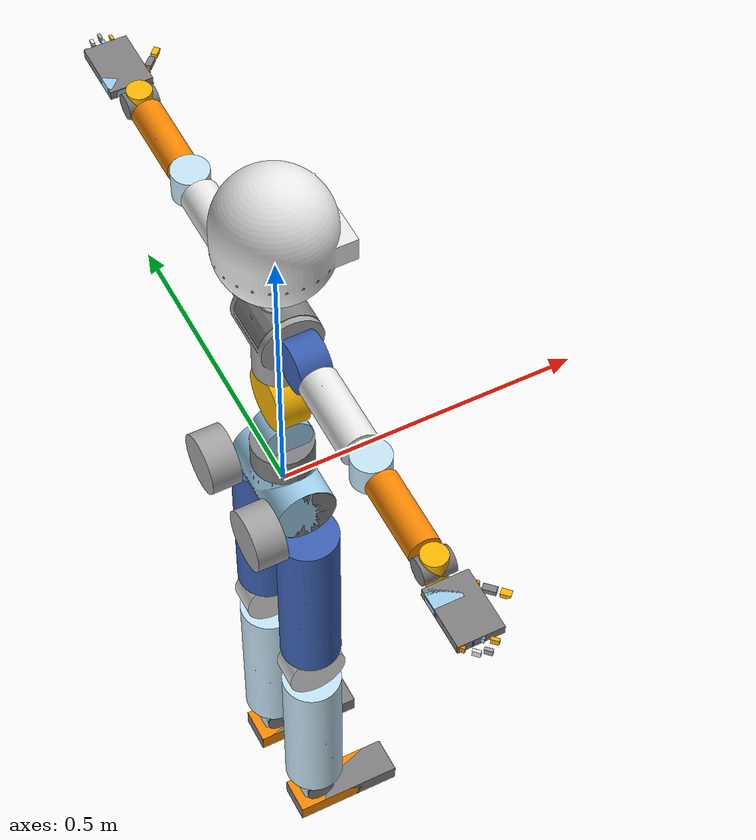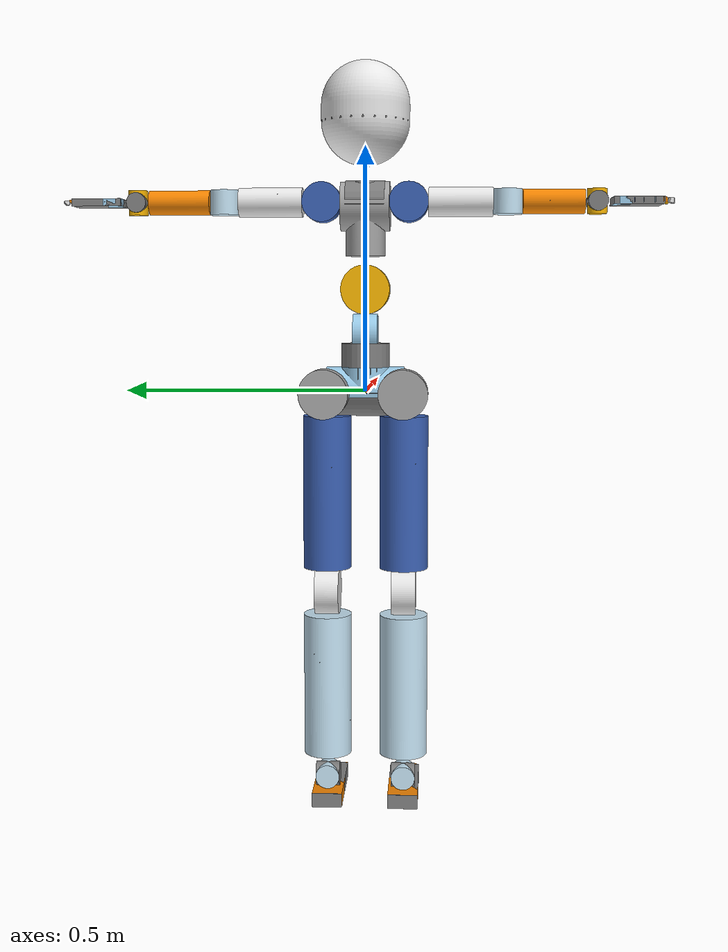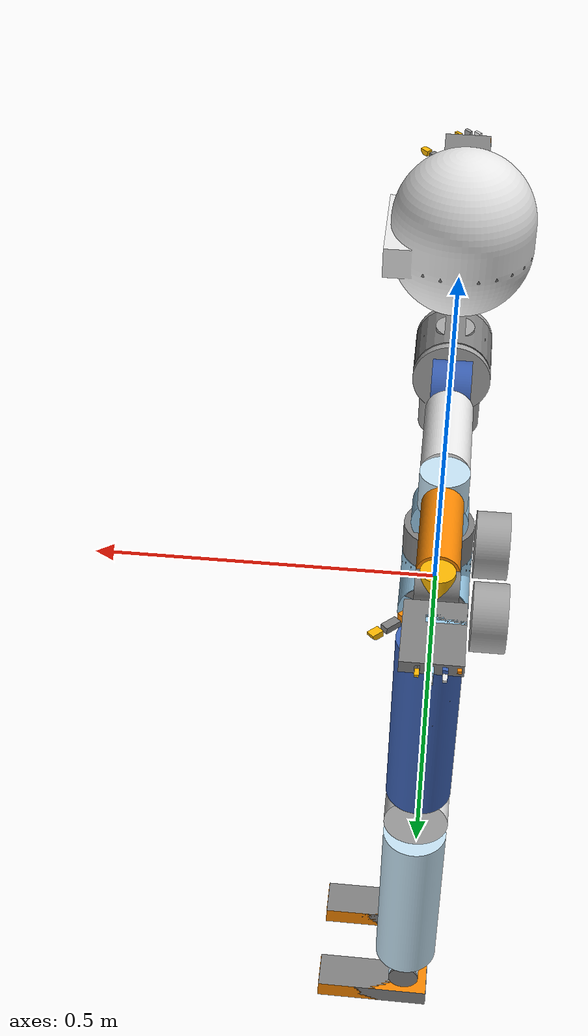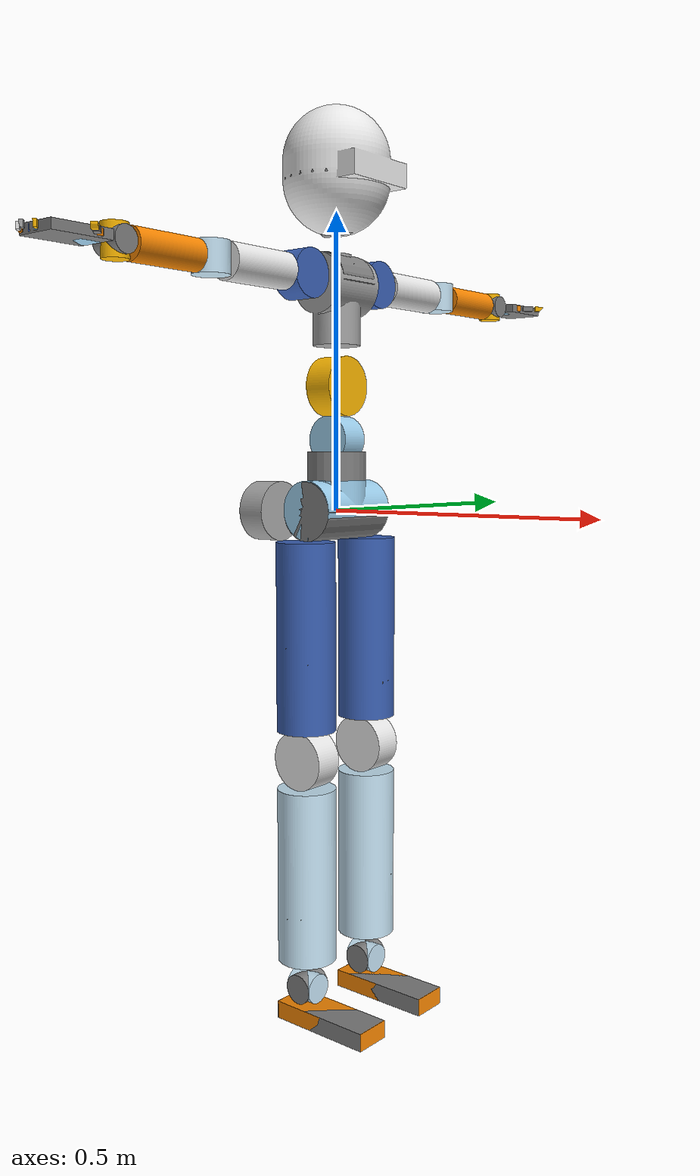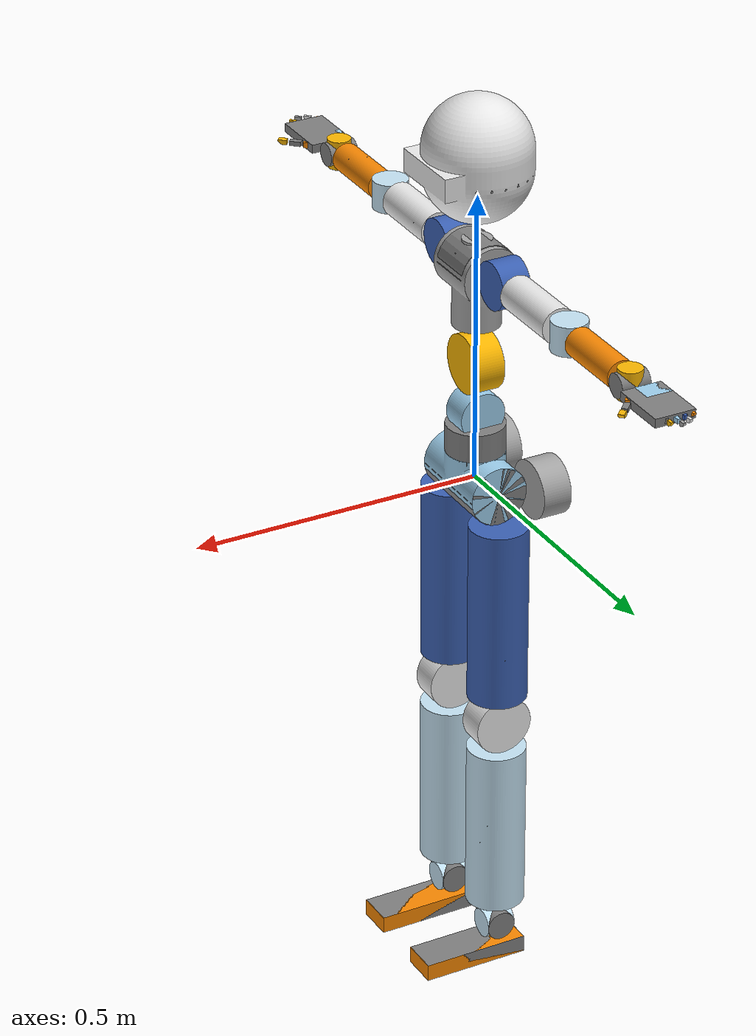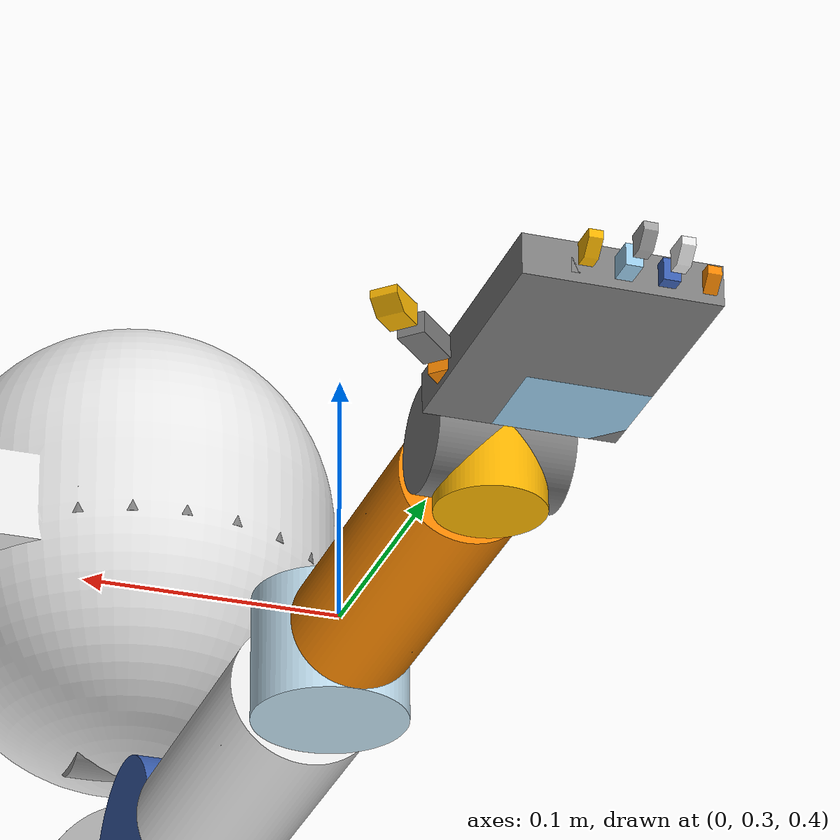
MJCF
<?xml version='1.0' encoding='utf-8'?>
<mujoco model="miku">
  <compiler angle="radian" meshdir="../meshes/" />

  <asset>
    <mesh name="pelvis_visual" content_type="model/stl" file="pelvis_visual.stl" />
    <mesh name="left_hip_pitch_visual" content_type="model/stl" file="left_hip_pitch_visual.stl" />
    <mesh name="left_hip_roll_visual" content_type="model/stl" file="left_hip_roll_visual.stl" />
    <mesh name="left_hip_yaw_visual" content_type="model/stl" file="left_hip_yaw_visual.stl" />
    <mesh name="left_knee_pitch_visual" content_type="model/stl" file="left_knee_pitch_visual.stl" />
    <mesh name="left_ankle_yaw_visual" content_type="model/stl" file="left_ankle_yaw_visual.stl" />
    <mesh name="left_ankle_roll_visual" content_type="model/stl" file="left_ankle_roll_visual.stl" />
    <mesh name="left_foot_visual" content_type="model/stl" file="left_foot_visual.stl" />
    <mesh name="right_hip_pitch_visual" content_type="model/stl" file="right_hip_pitch_visual.stl" />
    <mesh name="right_hip_roll_visual" content_type="model/stl" file="right_hip_roll_visual.stl" />
    <mesh name="right_hip_yaw_visual" content_type="model/stl" file="right_hip_yaw_visual.stl" />
    <mesh name="right_knee_pitch_visual" content_type="model/stl" file="right_knee_pitch_visual.stl" />
    <mesh name="right_ankle_yaw_visual" content_type="model/stl" file="right_ankle_yaw_visual.stl" />
    <mesh name="right_ankle_roll_visual" content_type="model/stl" file="right_ankle_roll_visual.stl" />
    <mesh name="right_foot_visual" content_type="model/stl" file="right_foot_visual.stl" />
    <mesh name="waist_yaw_visual" content_type="model/stl" file="waist_yaw_visual.stl" />
    <mesh name="waist_pitch_visual" content_type="model/stl" file="waist_pitch_visual.stl" />
    <mesh name="torso_visual" content_type="model/stl" file="torso_visual.stl" />
    <mesh name="left_shoulder_pitch_visual" content_type="model/stl"
      file="left_shoulder_pitch_visual.stl" />
    <mesh name="left_shoulder_roll_visual" content_type="model/stl"
      file="left_shoulder_roll_visual.stl" />
    <mesh name="left_shoulder_yaw_visual" content_type="model/stl"
      file="left_shoulder_yaw_visual.stl" />
    <mesh name="left_elbow_pitch_visual" content_type="model/stl" file="left_elbow_pitch_visual.stl" />
    <mesh name="left_wrist_yaw_visual" content_type="model/stl" file="left_wrist_yaw_visual.stl" />
    <mesh name="left_wrist_roll_visual" content_type="model/stl" file="left_wrist_roll_visual.stl" />
    <mesh name="left_hand_visual" content_type="model/stl" file="left_hand_visual.stl" />
    <mesh name="left_finger_1_j1_visual" content_type="model/stl" file="left_finger_1_j1_visual.stl" />
    <mesh name="left_finger_1_j2_visual" content_type="model/stl" file="left_finger_1_j2_visual.stl" />
    <mesh name="left_finger_1_j3_visual" content_type="model/stl" file="left_finger_1_j3_visual.stl" />
    <mesh name="left_finger_1_j4_visual" content_type="model/stl" file="left_finger_1_j4_visual.stl" />
    <mesh name="left_finger_2_j1_visual" content_type="model/stl" file="left_finger_2_j1_visual.stl" />
    <mesh name="left_finger_2_j2_visual" content_type="model/stl" file="left_finger_2_j2_visual.stl" />
    <mesh name="left_finger_2_j3_visual" content_type="model/stl" file="left_finger_2_j3_visual.stl" />
    <mesh name="left_finger_2_j4_visual" content_type="model/stl" file="left_finger_2_j4_visual.stl" />
    <mesh name="left_finger_3_j1_visual" content_type="model/stl" file="left_finger_3_j1_visual.stl" />
    <mesh name="left_finger_3_j2_visual" content_type="model/stl" file="left_finger_3_j2_visual.stl" />
    <mesh name="left_finger_3_j3_visual" content_type="model/stl" file="left_finger_3_j3_visual.stl" />
    <mesh name="left_finger_3_j4_visual" content_type="model/stl" file="left_finger_3_j4_visual.stl" />
    <mesh name="left_finger_4_j1_visual" content_type="model/stl" file="left_finger_4_j1_visual.stl" />
    <mesh name="left_finger_4_j2_visual" content_type="model/stl" file="left_finger_4_j2_visual.stl" />
    <mesh name="left_finger_4_j3_visual" content_type="model/stl" file="left_finger_4_j3_visual.stl" />
    <mesh name="left_finger_4_j4_visual" content_type="model/stl" file="left_finger_4_j4_visual.stl" />
    <mesh name="left_finger_5_j1_visual" content_type="model/stl" file="left_finger_5_j1_visual.stl" />
    <mesh name="left_finger_5_j2_visual" content_type="model/stl" file="left_finger_5_j2_visual.stl" />
    <mesh name="left_finger_5_j3_visual" content_type="model/stl" file="left_finger_5_j3_visual.stl" />
    <mesh name="left_finger_5_j4_visual" content_type="model/stl" file="left_finger_5_j4_visual.stl" />
    <mesh name="right_shoulder_pitch_visual" content_type="model/stl"
      file="right_shoulder_pitch_visual.stl" />
    <mesh name="right_shoulder_roll_visual" content_type="model/stl"
      file="right_shoulder_roll_visual.stl" />
    <mesh name="right_shoulder_yaw_visual" content_type="model/stl"
      file="right_shoulder_yaw_visual.stl" />
    <mesh name="right_elbow_pitch_visual" content_type="model/stl"
      file="right_elbow_pitch_visual.stl" />
    <mesh name="right_wrist_yaw_visual" content_type="model/stl" file="right_wrist_yaw_visual.stl" />
    <mesh name="right_wrist_roll_visual" content_type="model/stl" file="right_wrist_roll_visual.stl" />
    <mesh name="right_hand_visual" content_type="model/stl" file="right_hand_visual.stl" />
    <mesh name="right_finger_1_j1_visual" content_type="model/stl"
      file="right_finger_1_j1_visual.stl" />
    <mesh name="right_finger_1_j2_visual" content_type="model/stl"
      file="right_finger_1_j2_visual.stl" />
    <mesh name="right_finger_1_j3_visual" content_type="model/stl"
      file="right_finger_1_j3_visual.stl" />
    <mesh name="right_finger_1_j4_visual" content_type="model/stl"
      file="right_finger_1_j4_visual.stl" />
    <mesh name="right_finger_2_j1_visual" content_type="model/stl"
      file="right_finger_2_j1_visual.stl" />
    <mesh name="right_finger_2_j2_visual" content_type="model/stl"
      file="right_finger_2_j2_visual.stl" />
    <mesh name="right_finger_2_j3_visual" content_type="model/stl"
      file="right_finger_2_j3_visual.stl" />
    <mesh name="right_finger_2_j4_visual" content_type="model/stl"
      file="right_finger_2_j4_visual.stl" />
    <mesh name="right_finger_3_j1_visual" content_type="model/stl"
      file="right_finger_3_j1_visual.stl" />
    <mesh name="right_finger_3_j2_visual" content_type="model/stl"
      file="right_finger_3_j2_visual.stl" />
    <mesh name="right_finger_3_j3_visual" content_type="model/stl"
      file="right_finger_3_j3_visual.stl" />
    <mesh name="right_finger_3_j4_visual" content_type="model/stl"
      file="right_finger_3_j4_visual.stl" />
    <mesh name="right_finger_4_j1_visual" content_type="model/stl"
      file="right_finger_4_j1_visual.stl" />
    <mesh name="right_finger_4_j2_visual" content_type="model/stl"
      file="right_finger_4_j2_visual.stl" />
    <mesh name="right_finger_4_j3_visual" content_type="model/stl"
      file="right_finger_4_j3_visual.stl" />
    <mesh name="right_finger_4_j4_visual" content_type="model/stl"
      file="right_finger_4_j4_visual.stl" />
    <mesh name="right_finger_5_j1_visual" content_type="model/stl"
      file="right_finger_5_j1_visual.stl" />
    <mesh name="right_finger_5_j2_visual" content_type="model/stl"
      file="right_finger_5_j2_visual.stl" />
    <mesh name="right_finger_5_j3_visual" content_type="model/stl"
      file="right_finger_5_j3_visual.stl" />
    <mesh name="right_finger_5_j4_visual" content_type="model/stl"
      file="right_finger_5_j4_visual.stl" />
    <mesh name="neck_yaw_visual" content_type="model/stl" file="neck_yaw_visual.stl" />
    <mesh name="neck_roll_visual" content_type="model/stl" file="neck_roll_visual.stl" />
    <mesh name="head_visual" content_type="model/stl" file="head_visual.stl" />
  </asset>

  <worldbody>
    <body name="pelvis">
      <joint name="floating_base_joint" type="free" limited="false" actuatorfrclimited="false"
        frictionloss="0.05" armature="0.001" />
      <inertial pos="9.857e-09 2.3583e-08 0.00318033"
        quat="0.707105 0.707108 4.3511e-05 -4.35108e-05" mass="1.63182"
        diaginertia="0.0044708 0.00445476 0.00215919" />
      <geom size="0.05 0.05" pos="0 0 0.05" quat="0.707105 0 0 -0.707108" type="cylinder" />
      <geom size="0.05 0.08" quat="0.499998 0.5 0.5 -0.500002" type="cylinder" />
      <geom pos="9.857e-09 2.3583e-08 0.00318033" quat="1 0 0 0" type="mesh" contype="0"
        conaffinity="0" group="1" density="0" rgba="0.615686 0.811765 0.929412 1"
        mesh="pelvis_visual" />
      <body name="left_hip_pitch" pos="1.36e-09 0.08 1.6286e-08" quat="0.642787 -0.766045 0 0">
        <inertial pos="-0.08 0 0" mass="0.486947" diaginertia="0.000608684 0.000405789 0.000405789" />
        <joint name="left_hip_pitch" pos="0 0 0" axis="0 0 1" range="-2.35619 0.785398"
          actuatorfrcrange="-100 100" frictionloss="0.1" armature="0.01" />
        <geom pos="-0.08 0 0" quat="0.642787 0.766045 0 0" type="mesh" contype="0" conaffinity="0"
          group="1" density="0" rgba="0.647059 0.647059 0.647059 1" mesh="left_hip_pitch_visual" />
        <body name="left_hip_roll" quat="0.704416 0.0616296 0.704416 0.0616296">
          <inertial pos="0 0.21 0" quat="0.707107 0.707107 0 0" mass="3.11646"
            diaginertia="0.0285416 0.0285416 0.00389557" />
          <joint name="left_hip_roll" pos="0 0 0" axis="0 0 1" range="-0.261799 1.5708"
            actuatorfrcrange="-100 100" frictionloss="0.1" armature="0.01" />
          <geom size="0.05 0.1" pos="0 0.21 0" quat="0.707105 0.707108 0 0" type="cylinder" />
          <geom pos="0 0.21 0" quat="0.499998 0.5 -0.5 0.500002" type="mesh" contype="0"
            conaffinity="0" group="1" density="0" rgba="0.231373 0.380392 0.705882 1"
            mesh="left_hip_roll_visual" />
          <body name="left_hip_yaw" quat="0.499998 0.5 -0.5 0.500002">
            <inertial pos="0 0 -0.42" quat="0.707107 0 0 0.707107" mass="0.486947"
              diaginertia="0.000608684 0.000405789 0.000405789" />
            <joint name="left_hip_yaw" pos="0 0 0" axis="0 0 1" range="-0.785398 0.785398"
              actuatorfrcrange="-100 100" frictionloss="0.1" armature="0.01" />
            <geom pos="0 0 -0.42" quat="1 0 0 0" type="mesh" contype="0" conaffinity="0" group="1"
              density="0" rgba="0.917647 0.917647 0.917647 1" mesh="left_hip_yaw_visual" />
            <body name="left_knee_pitch" pos="0 0 -0.42" quat="0.707105 -0.707108 0 0">
              <inertial pos="0 0.2 0" quat="0.707107 0.707107 0 0" mass="2.92168"
                diaginertia="0.0237387 0.0237387 0.0036521" />
              <joint name="left_knee_pitch" pos="0 0 0" axis="0 0 1" range="0 2.35619"
                actuatorfrcrange="-100 100" frictionloss="0.1" armature="0.01" />
              <geom size="0.05 0.08" pos="0 0.2 0" quat="0.499998 0.5 0.5 -0.500002" type="cylinder" />
              <geom pos="0 0.2 0" quat="0.707105 0.707108 0 0" type="mesh" contype="0"
                conaffinity="0" group="1" density="0" rgba="0.768627 0.886275 0.952941 1"
                mesh="left_knee_pitch_visual" />
              <body name="left_ankle_yaw" pos="0 0.4 0" quat="0.707105 0.707108 0 0">
                <inertial pos="0 0 0" quat="0.5 0.5 0.5 0.5" mass="0.121737"
                  diaginertia="4.43832e-05 4.43832e-05 3.80427e-05" />
                <joint name="left_ankle_yaw" pos="0 0 0" axis="0 0 1" range="-0.785398 0.785398"
                  actuatorfrcrange="-100 100" frictionloss="0.1" armature="0.01" />
                <geom type="mesh" contype="0" conaffinity="0" group="1" density="0"
                  rgba="0.768627 0.886275 0.952941 1" mesh="left_ankle_yaw_visual" />
                <body name="left_ankle_roll" quat="0.499998 -0.5 0.500002 -0.5">
                  <inertial pos="0 0 0" quat="0.5 0.5 0.5 0.5" mass="0.121737"
                    diaginertia="4.43832e-05 4.43832e-05 3.80427e-05" />
                  <joint name="left_ankle_roll" pos="0 0 0" axis="0 0 1" range="-0.349066 0.349066"
                    actuatorfrcrange="-100 100" frictionloss="0.1" armature="0.01" />
                  <geom quat="0.499998 0.5 -0.5 0.500002" type="mesh" contype="0" conaffinity="0"
                    group="1" density="0" rgba="0.498039 0.498039 0.498039 1"
                    mesh="left_ankle_roll_visual" />
                  <body name="left_foot" quat="0.707105 0 -0.707108 0">
                    <inertial pos="0.0525 0.045 0" quat="0.5 0.5 0.5 0.5" mass="0.433566"
                      diaginertia="0.00137997 0.00126908 0.000175919" />
                    <joint name="left_ankle_pitch" pos="0 0 0" axis="0 0 1"
                      range="-0.785398 0.785398" actuatorfrcrange="-100 100" frictionloss="0.1"
                      armature="0.01" />
                    <geom size="0.0315 0.0925 0.015" pos="0.052 0.045 0"
                      quat="0.499998 0.5 0.5 -0.500002" type="box" />
                    <geom pos="0.0525 0.045 0" quat="0.707105 0.707108 0 0" type="mesh" contype="0"
                      conaffinity="0" group="1" density="0" rgba="0.972549 0.529412 0.00392157 1"
                      mesh="left_foot_visual" />
                  </body>
                </body>
              </body>
            </body>
          </body>
        </body>
      </body>
      <body name="right_hip_pitch" pos="1.36e-09 -0.08 -1.6286e-08" quat="0.766046 -0.642786 0 0">
        <inertial pos="-0.08 0 0" mass="0.486947" diaginertia="0.000608684 0.000405789 0.000405789" />
        <joint name="right_hip_pitch" pos="0 0 0" axis="0 0 1" range="-2.35619 0.785398"
          actuatorfrcrange="-100 100" frictionloss="0.1" armature="0.01" />
        <geom pos="-0.08 0 0" quat="0.766046 0.642786 0 0" type="mesh" contype="0" conaffinity="0"
          group="1" density="0" rgba="0.647059 0.647059 0.647059 1" mesh="right_hip_pitch_visual" />
        <body name="right_hip_roll" quat="0.704416 -0.0616296 0.704416 -0.0616296">
          <inertial pos="0 0.21 0" quat="0.707107 0.707107 0 0" mass="3.11646"
            diaginertia="0.0285416 0.0285416 0.00389557" />
          <joint name="right_hip_roll" pos="0 0 0" axis="0 0 1" range="-1.5708 0.261799"
            actuatorfrcrange="-100 100" frictionloss="0.1" armature="0.01" />
          <geom size="0.05 0.1" pos="0 0.21 0" quat="0.707105 0.707108 0 0" type="cylinder" />
          <geom pos="0 0.21 0" quat="0.499998 0.5 -0.5 0.500002" type="mesh" contype="0"
            conaffinity="0" group="1" density="0" rgba="0.231373 0.380392 0.705882 1"
            mesh="right_hip_roll_visual" />
          <body name="right_hip_yaw" quat="0.499998 0.5 -0.5 0.500002">
            <inertial pos="0 0 -0.42" quat="0.707107 0 0 0.707107" mass="0.486947"
              diaginertia="0.000608684 0.000405789 0.000405789" />
            <joint name="right_hip_yaw" pos="0 0 0" axis="0 0 1" range="-0.785398 0.785398"
              actuatorfrcrange="-100 100" frictionloss="0.1" armature="0.01" />
            <geom pos="0 0 -0.42" quat="1 0 0 0" type="mesh" contype="0" conaffinity="0" group="1"
              density="0" rgba="0.917647 0.917647 0.917647 1" mesh="right_hip_yaw_visual" />
            <body name="right_knee_pitch" pos="0 0 -0.42" quat="0.707105 -0.707108 0 0">
              <inertial pos="0 0.2 0" quat="0.707107 0.707107 0 0" mass="2.92168"
                diaginertia="0.0237387 0.0237387 0.0036521" />
              <joint name="right_knee_pitch" pos="0 0 0" axis="0 0 1" range="0 2.35619"
                actuatorfrcrange="-100 100" frictionloss="0.1" armature="0.01" />
              <geom size="0.05 0.08" pos="0 0.2 0" quat="0.499998 0.5 0.5 -0.500002" type="cylinder" />
              <geom pos="0 0.2 0" quat="0.707105 0.707108 0 0" type="mesh" contype="0"
                conaffinity="0" group="1" density="0" rgba="0.768627 0.886275 0.952941 1"
                mesh="right_knee_pitch_visual" />
              <body name="right_ankle_yaw" pos="0 0.4 0" quat="0.707105 0.707108 0 0">
                <inertial pos="0 0 1e-12" quat="0.5 0.5 0.5 0.5" mass="0.121737"
                  diaginertia="4.43832e-05 4.43832e-05 3.80427e-05" />
                <joint name="right_ankle_yaw" pos="0 0 0" axis="0 0 1" range="-0.785398 0.785398"
                  actuatorfrcrange="-100 100" frictionloss="0.1" armature="0.01" />
                <geom pos="0 0 0" quat="1 0 0 0" type="mesh" contype="0" conaffinity="0" group="1"
                  density="0" rgba="0.768627 0.886275 0.952941 1" mesh="right_ankle_yaw_visual" />
                <body name="right_ankle_roll" quat="0.499998 -0.5 0.500002 -0.5">
                  <inertial pos="0 0 0" quat="0.5 0.5 0.5 0.5" mass="0.121737"
                    diaginertia="4.43832e-05 4.43832e-05 3.80427e-05" />
                  <joint name="right_ankle_roll" pos="0 0 0" axis="0 0 1" range="-0.349066 0.349066"
                    actuatorfrcrange="-100 100" frictionloss="0.1" armature="0.01" />
                  <geom quat="0.499998 0.5 -0.5 0.500002" type="mesh" contype="0" conaffinity="0"
                    group="1" density="0" rgba="0.498039 0.498039 0.498039 1"
                    mesh="right_ankle_roll_visual" />
                  <body name="right_foot" quat="0.707105 0 -0.707108 0">
                    <inertial pos="0.0525 0.045 0" quat="0.5 0.5 0.5 0.5" mass="0.433566"
                      diaginertia="0.00137997 0.00126908 0.000175919" />
                    <joint name="right_ankle_pitch" pos="0 0 0" axis="0 0 1"
                      range="-0.785398 0.785398" actuatorfrcrange="-100 100" frictionloss="0.1"
                      armature="0.01" />
                    <geom size="0.0315 0.0925 0.015" pos="0.052 0.045 0"
                      quat="0.499998 0.5 0.5 -0.500002" type="box" />
                    <geom pos="0.0525 0.045 0" quat="0.707105 0.707108 0 0" type="mesh" contype="0"
                      conaffinity="0" group="1" density="0" rgba="0.972549 0.529412 0.00392157 1"
                      mesh="right_foot_visual" />
                  </body>
                </body>
              </body>
            </body>
          </body>
        </body>
      </body>
      <body name="waist_yaw" pos="0 0 0.12">
        <inertial pos="0 0 0" quat="0.707107 0 0 0.707107" mass="0.311646"
          diaginertia="0.000249317 0.000189585 0.000189585" />
        <joint name="waist_yaw" pos="0 0 0" axis="0 0 1" range="-1.5708 1.5708"
          actuatorfrcrange="-100 100" frictionloss="0.1" armature="0.01" />
        <geom type="mesh" contype="0" conaffinity="0" group="1" density="0"
          rgba="0.615686 0.811765 0.929412 1" mesh="waist_yaw_visual" />
        <body name="waist_pitch" quat="9.38184e-07 9.38187e-07 0.707108 0.707105">
          <inertial pos="0 0.09 0" mass="0.486947" diaginertia="0.000608684 0.000405789 0.000405789" />
          <joint name="waist_pitch" pos="0 0 0" axis="0 0 1" range="-0.785398 1.5708"
            actuatorfrcrange="-100 100" frictionloss="0.1" armature="0.01" />
          <geom pos="0 0.09 0" quat="9.38184e-07 9.38187e-07 -0.707108 -0.707105" type="mesh"
            contype="0" conaffinity="0" group="1" density="0" rgba="0.980392 0.713725 0.00392157 1"
            mesh="waist_pitch_visual" />
          <body name="torso" pos="0 0.09 0" quat="0.707105 0 -0.707108 0">
            <inertial pos="-1.827e-08 0.149634 4.13491e-07" quat="0.499989 0.5 -0.50001 0.500001"
              mass="1.30495" diaginertia="0.00287674 0.00269369 0.00168245" />
            <joint name="waist_roll" pos="0 0 0" axis="0 0 1" range="-1.0472 1.0472"
              actuatorfrcrange="-100 100" frictionloss="0.1" armature="0.01" />
            <geom size="0.04 0.06" pos="0 0.14 0" quat="9.38184e-07 9.38187e-07 -0.707108 -0.707105"
              type="cylinder" />
            <geom size="0.05 0.04" pos="0 0.17 0" quat="0.499998 0.5 -0.500002 -0.5" type="cylinder" />
            <geom pos="-1.827e-08 0.149634 4.13491e-07" quat="0.499998 -0.5 -0.5 -0.500002"
              type="mesh" contype="0" conaffinity="0" group="1" density="0"
              rgba="0.647059 0.647059 0.647059 1" mesh="torso_visual" />
            <body name="left_shoulder_pitch" pos="0.0887752 0.176946 0"
              quat="0.0616282 -0.704415 -0.0616284 -0.704417">
              <inertial pos="0 0 0" mass="0.311646"
                diaginertia="0.000249317 0.000189585 0.000189585" />
              <joint name="left_shoulder_pitch" pos="0 0 0" axis="0 0 1" range="-3.14159 0.785398"
                actuatorfrcrange="-100 100" frictionloss="0.1" armature="0.01" />
              <geom quat="0.766046 0.642786 0 0" type="mesh" contype="0" conaffinity="0" group="1"
                density="0" rgba="0.231373 0.380392 0.705882 1" mesh="left_shoulder_pitch_visual" />
              <body name="left_shoulder_roll" quat="0.541674 0.454519 0.541677 0.454519">
                <inertial pos="0 0.105 0" quat="0.707107 0.707107 0 0" mass="0.455782"
                  diaginertia="0.000744444 0.000744444 0.000205102" />
                <joint name="left_shoulder_roll" pos="0 0 0" axis="0 0 1" range="-1.74533 1.5708"
                  actuatorfrcrange="-100 100" frictionloss="0.1" armature="0.01" />
                <geom size="0.03 0.04" pos="0 0.105 0" quat="0.707105 0.707108 0 0" type="cylinder" />
                <geom pos="0 0.105 0" quat="0.707105 0 -0.707108 0" type="mesh" contype="0"
                  conaffinity="0" group="1" density="0" rgba="0.917647 0.917647 0.917647 1"
                  mesh="left_shoulder_roll_visual" />
                <body name="left_shoulder_yaw" quat="0.499998 0.5 -0.5 0.500002">
                  <inertial pos="0 0 -0.2" quat="0.707107 0 0 0.707107" mass="0.175301"
                    diaginertia="7.88854e-05 7.59637e-05 7.59637e-05" />
                  <joint name="left_shoulder_yaw" pos="0 0 0" axis="0 0 1" range="-1.5708 1.5708"
                    actuatorfrcrange="-100 100" frictionloss="0.1" armature="0.01" />
                  <geom pos="0 0 -0.2" quat="0.707105 -0.707108 0 0" type="mesh" contype="0"
                    conaffinity="0" group="1" density="0" rgba="0.768627 0.886275 0.952941 1"
                    mesh="left_shoulder_yaw_visual" />
                  <body name="left_elbow_pitch" pos="0 0 -0.2" quat="0.707105 -0.707108 0 0">
                    <inertial pos="0 0.0925 0" quat="0.707107 0.707107 0 0" mass="0.304342"
                      diaginertia="0.000443832 0.000443832 9.51068e-05" />
                    <joint name="left_elbow_pitch" pos="0 0 0" axis="0 0 1" range="-2.35619 0"
                      actuatorfrcrange="-100 100" frictionloss="0.1" armature="0.01" />
                    <geom size="0.025 0.04" pos="0 0.095 0" quat="0.499998 0.5 0.5 -0.500002"
                      type="cylinder" />
                    <geom pos="0 0.0925 0" quat="1 0 0 0" type="mesh" contype="0" conaffinity="0"
                      group="1" density="0" rgba="0.972549 0.529412 0.00392157 1"
                      mesh="left_elbow_pitch_visual" />
                    <body name="left_wrist_yaw" pos="0 0.18 0" quat="0.707105 0.707108 0 0">
                      <inertial pos="0 0 0" quat="0.707107 0.707107 0 0" mass="0.0779115"
                        diaginertia="2.40227e-05 2.40227e-05 1.55823e-05" />
                      <joint name="left_wrist_yaw" pos="0 0 0" axis="0 0 1" range="-1.5708 1.5708"
                        actuatorfrcrange="-100 100" frictionloss="0.1" armature="0.01" />
                      <geom quat="0.707105 -0.707108 0 0" type="mesh" contype="0" conaffinity="0"
                        group="1" density="0" rgba="0.980392 0.713725 0.00392157 1"
                        mesh="left_wrist_yaw_visual" />
                      <body name="left_wrist_roll" quat="0.707105 -0.707108 0 0">
                        <inertial pos="0 0 0" quat="0.5 0.5 0.5 0.5" mass="0.0779115"
                          diaginertia="2.40227e-05 2.40227e-05 1.55823e-05" />
                        <joint name="left_wrist_roll" pos="0 0 0" axis="0 0 1"
                          range="-0.349066 0.349066" actuatorfrcrange="-100 100" frictionloss="0.1"
                          armature="0.01" />
                        <geom type="mesh" contype="0" conaffinity="0" group="1" density="0"
                          rgba="0.498039 0.498039 0.498039 1" mesh="left_wrist_roll_visual" />
                        <body name="left_hand" quat="0.707105 0 0.707108 0">
                          <inertial pos="0 0.0479645 -0.0118716" quat="0.997543 0.0700549 0 0"
                            mass="0.028365" diaginertia="7.37812e-06 5.15381e-06 3.28799e-06" />
                          <joint name="left_wrist_pitch" pos="0 0 0" axis="0 0 1"
                            range="-1.5708 1.5708" actuatorfrcrange="-100 100" frictionloss="0.1"
                            armature="0.01" />
                          <geom size="0.05 0.035 0.0075" pos="0 0.08 0"
                            quat="0.499998 0.5 -0.500002 -0.5" type="box" />
                          <geom pos="0 0.0479645 -0.0118716" quat="0.707105 0 -0.707108 0"
                            type="mesh" contype="0" conaffinity="0" group="1" density="0"
                            rgba="0.615686 0.811765 0.929412 1" mesh="left_hand_visual" />
                          <body name="left_finger_1_j1" pos="0 0.035 0.015"
                            quat="0.92388 0.382683 0 0">
                            <inertial pos="0 0.0025 0" quat="0.707107 0 0 0.707107" mass="0.000744"
                              diaginertia="1.5128e-08 1.0478e-08 7.75e-09" />
                            <joint name="left_finger1_j1" pos="0 0 0" axis="0 0 1"
                              range="-1.91986 0.0872665" actuatorfrcrange="-100 100"
                              frictionloss="0.05" armature="0.001" />
                            <geom pos="0 0.0025 0" quat="0.65328 -0.270598 -0.653282 0.270598"
                              type="mesh" contype="0" conaffinity="0" group="1" density="0"
                              rgba="0.498039 0.498039 0.498039 1" mesh="left_finger_1_j1_visual" />
                            <body name="left_finger_1_j2" pos="0 0.01 0"
                              quat="0.707105 0 -0.707108 0">
                              <inertial pos="0 0.01 0" quat="0.5 0.5 -0.5 0.5" mass="0.002976"
                                diaginertia="1.34912e-07 1.24e-07 6.0512e-08" />
                              <joint name="left_finger1_j2" pos="0 0 0" axis="0 0 1"
                                range="-0.349066 0.349066" actuatorfrcrange="-100 100"
                                frictionloss="0.05" armature="0.001" />
                              <geom pos="0 0.01 0" quat="0.92388 0 0 0.382683" type="mesh"
                                contype="0" conaffinity="0" group="1" density="0"
                                rgba="0.972549 0.529412 0.00392157 1" mesh="left_finger_1_j2_visual" />
                              <body name="left_finger_1_j3" pos="0 0.025 0"
                                quat="0.707105 0 0.707108 0">
                                <inertial pos="0 0.01 0" quat="0.707107 0.707107 0 0"
                                  mass="0.001984" diaginertia="8.2667e-08 7.6715e-08 2.7115e-08" />
                                <joint name="left_finger1_j3" pos="0 0 0" axis="0 0 1"
                                  range="-1.91986 0.0872665" actuatorfrcrange="-100 100"
                                  frictionloss="0.05" armature="0.001" />
                                <geom pos="0 0.01 0" quat="0.65328 -0.270598 -0.653282 0.270598"
                                  type="mesh" contype="0" conaffinity="0" group="1" density="0"
                                  rgba="0.498039 0.498039 0.498039 1" mesh="left_finger_1_j3_visual" />
                                <body name="left_finger_1_j4" pos="0 0.025 0">
                                  <inertial pos="-0.000271318 0.00682171 0"
                                    quat="0.705239 0.705239 0.0513544 0.0513544" mass="0.001333"
                                    diaginertia="3.3234e-08 2.8576e-08 1.7558e-08" />
                                  <joint name="left_finger1_j4" pos="0 0 0" axis="0 0 1"
                                    range="-1.91986 0.0872665" actuatorfrcrange="-100 100"
                                    frictionloss="0.05" armature="0.001" />
                                  <geom pos="-0.000271318 0.00682171 0"
                                    quat="0.65328 -0.270598 -0.653282 0.270598" type="mesh"
                                    contype="0" conaffinity="0" group="1" density="0"
                                    rgba="0.980392 0.713725 0.00392157 1"
                                    mesh="left_finger_1_j4_visual" />
                                </body>
                              </body>
                            </body>
                          </body>
                          <body name="left_finger_2_j1" pos="0 0.07 0.015">
                            <inertial pos="0 0.0025 0" quat="0.5 0.5 0.5 0.5" mass="0.000496"
                              diaginertia="6.779e-09 5.167e-09 3.679e-09" />
                            <joint name="left_finger2_j1" pos="0 0 0" axis="0 0 1"
                              range="-1.91986 0.0872665" actuatorfrcrange="-100 100"
                              frictionloss="0.05" armature="0.001" />
                            <geom pos="0 0.0025 0" quat="0.707105 0 -0.707108 0" type="mesh"
                              contype="0" conaffinity="0" group="1" density="0"
                              rgba="0.980392 0.713725 0.00392157 1" mesh="left_finger_2_j1_visual" />
                            <body name="left_finger_2_j2" pos="0 0.01 0"
                              quat="0.707105 0 -0.707108 0">
                              <inertial pos="0 0.0125 0" quat="0.707107 0.707107 0 0" mass="0.00248"
                                diaginertia="1.49833e-07 1.42393e-07 3.3893e-08" />
                              <joint name="left_finger2_j2" pos="0 0 0" axis="0 0 1"
                                range="-0.349066 0.349066" actuatorfrcrange="-100 100"
                                frictionloss="0.05" armature="0.001" />
                              <geom pos="0 0.0125 0" quat="1 0 0 0" type="mesh" contype="0"
                                conaffinity="0" group="1" density="0"
                                rgba="0.647059 0.647059 0.647059 1" mesh="left_finger_2_j2_visual" />
                              <body name="left_finger_2_j3" pos="0 0.03 0"
                                quat="0.707105 0 0.707108 0">
                                <inertial pos="0 0.01 0" quat="0.5 0.5 -0.5 0.5" mass="0.0011904"
                                  diaginertia="4.6029e-08 4.3251e-08 9.92e-09" />
                                <joint name="left_finger2_j3" pos="0 0 0" axis="0 0 1"
                                  range="-1.91986 0.0872665" actuatorfrcrange="-100 100"
                                  frictionloss="0.05" armature="0.001" />
                                <geom pos="0 0.01 0" quat="0.707105 0 -0.707108 0" type="mesh"
                                  contype="0" conaffinity="0" group="1" density="0"
                                  rgba="0.498039 0.498039 0.498039 1" mesh="left_finger_2_j3_visual" />
                                <body name="left_finger_2_j4" pos="0 0.025 0">
                                  <inertial pos="-0.000432099 0.00438272 0"
                                    quat="0.370021 0.602565 -0.370021 0.602565" mass="0.0004185"
                                    diaginertia="5.043e-09 4.21225e-09 2.57375e-09" />
                                  <joint name="left_finger2_j4" pos="0 0 0" axis="0 0 1"
                                    range="-1.91986 0.0872665" actuatorfrcrange="-100 100"
                                    frictionloss="0.05" armature="0.001" />
                                  <geom pos="-0.000432099 0.00438272 0"
                                    quat="0.707105 0 -0.707108 0" type="mesh" contype="0"
                                    conaffinity="0" group="1" density="0"
                                    rgba="0.980392 0.713725 0.00392157 1"
                                    mesh="left_finger_2_j4_visual" />
                                </body>
                              </body>
                            </body>
                          </body>
                          <body name="left_finger_3_j1" pos="0 0.07 0">
                            <inertial pos="0 0.0025 0" quat="0.5 0.5 0.5 0.5" mass="0.000496"
                              diaginertia="6.779e-09 5.167e-09 3.679e-09" />
                            <joint name="left_finger3_j1" pos="0 0 0" axis="0 0 1"
                              range="-1.91986 0.0872665" actuatorfrcrange="-100 100"
                              frictionloss="0.05" armature="0.001" />
                            <geom pos="0 0.0025 0" quat="0.707105 0 -0.707108 0" type="mesh"
                              contype="0" conaffinity="0" group="1" density="0"
                              rgba="0.615686 0.811765 0.929412 1" mesh="left_finger_3_j1_visual" />
                            <body name="left_finger_3_j2" pos="0 0.01 0"
                              quat="0.707105 0 -0.707108 0">
                              <inertial pos="0 0.015 0" quat="0.707107 0.707107 0 0" mass="0.002976"
                                diaginertia="2.48e-07 2.39072e-07 4.0672e-08" />
                              <joint name="left_finger3_j2" pos="0 0 0" axis="0 0 1"
                                range="-0.349066 0.349066" actuatorfrcrange="-100 100"
                                frictionloss="0.05" armature="0.001" />
                              <geom pos="0 0.015 0" quat="1 0 0 0" type="mesh" contype="0"
                                conaffinity="0" group="1" density="0"
                                rgba="0.231373 0.380392 0.705882 1" mesh="left_finger_3_j2_visual" />
                              <body name="left_finger_3_j3" pos="0 0.035 0"
                                quat="0.707105 0 0.707108 0">
                                <inertial pos="0 0.0125 0" quat="0.5 0.5 -0.5 0.5" mass="0.001488"
                                  diaginertia="8.5436e-08 8.1964e-08 1.24e-08" />
                                <joint name="left_finger3_j3" pos="0 0 0" axis="0 0 1"
                                  range="-1.91986 0.0872665" actuatorfrcrange="-100 100"
                                  frictionloss="0.05" armature="0.001" />
                                <geom pos="0 0.0125 0" quat="0.707105 0 -0.707108 0" type="mesh"
                                  contype="0" conaffinity="0" group="1" density="0"
                                  rgba="0.615686 0.811765 0.929412 1" mesh="left_finger_3_j3_visual" />
                                <body name="left_finger_3_j4" pos="0 0.03 0">
                                  <inertial pos="-0.000432099 0.00438272 0"
                                    quat="0.370021 0.602565 -0.370021 0.602565" mass="0.0004185"
                                    diaginertia="5.043e-09 4.21225e-09 2.57375e-09" />
                                  <joint name="left_finger3_j4" pos="0 0 0" axis="0 0 1"
                                    range="-1.91986 0.0872665" actuatorfrcrange="-100 100"
                                    frictionloss="0.05" armature="0.001" />
                                  <geom pos="-0.000432099 0.00438272 0"
                                    quat="0.707105 0 -0.707108 0" type="mesh" contype="0"
                                    conaffinity="0" group="1" density="0"
                                    rgba="0.647059 0.647059 0.647059 1"
                                    mesh="left_finger_3_j4_visual" />
                                </body>
                              </body>
                            </body>
                          </body>
                          <body name="left_finger_4_j1" pos="0 0.07 -0.015">
                            <inertial pos="0 0.0025 0" quat="0.5 0.5 0.5 0.5" mass="0.000496"
                              diaginertia="6.779e-09 5.167e-09 3.679e-09" />
                            <joint name="left_finger4_j1" pos="0 0 0" axis="0 0 1"
                              range="-1.91986 0.0872665" actuatorfrcrange="-100 100"
                              frictionloss="0.05" armature="0.001" />
                            <geom pos="0 0.0025 0" quat="0.707105 0 -0.707108 0" type="mesh"
                              contype="0" conaffinity="0" group="1" density="0"
                              rgba="0.647059 0.647059 0.647059 1" mesh="left_finger_4_j1_visual" />
                            <body name="left_finger_4_j2" pos="0 0.01 0"
                              quat="0.707105 0 -0.707108 0">
                              <inertial pos="0 0.015 0" quat="0.707107 0.707107 0 0" mass="0.002976"
                                diaginertia="2.48e-07 2.39072e-07 4.0672e-08" />
                              <joint name="left_finger4_j2" pos="0 0 0" axis="0 0 1"
                                range="-0.349066 0.349066" actuatorfrcrange="-100 100"
                                frictionloss="0.05" armature="0.001" />
                              <geom pos="0 0.015 0" quat="1 0 0 0" type="mesh" contype="0"
                                conaffinity="0" group="1" density="0"
                                rgba="0.917647 0.917647 0.917647 1" mesh="left_finger_4_j2_visual" />
                              <body name="left_finger_4_j3" pos="0 0.035 0"
                                quat="0.707105 0 0.707108 0">
                                <inertial pos="0 0.01 0" quat="0.5 0.5 -0.5 0.5" mass="0.0011904"
                                  diaginertia="4.6029e-08 4.3251e-08 9.92e-09" />
                                <joint name="left_finger4_j3" pos="0 0 0" axis="0 0 1"
                                  range="-1.91986 0.0872665" actuatorfrcrange="-100 100"
                                  frictionloss="0.05" armature="0.001" />
                                <geom pos="0 0.01 0" quat="0.707105 0 -0.707108 0" type="mesh"
                                  contype="0" conaffinity="0" group="1" density="0"
                                  rgba="0.231373 0.380392 0.705882 1" mesh="left_finger_4_j3_visual" />
                                <body name="left_finger_4_j4" pos="0 0.025 0">
                                  <inertial pos="-0.000432099 0.00438272 0"
                                    quat="0.370021 0.602565 -0.370021 0.602565" mass="0.0004185"
                                    diaginertia="5.043e-09 4.21225e-09 2.57375e-09" />
                                  <joint name="left_finger4_j4" pos="0 0 0" axis="0 0 1"
                                    range="-1.91986 0.0872665" actuatorfrcrange="-100 100"
                                    frictionloss="0.05" armature="0.001" />
                                  <geom pos="-0.000432099 0.00438272 0"
                                    quat="0.707105 0 -0.707108 0" type="mesh" contype="0"
                                    conaffinity="0" group="1" density="0"
                                    rgba="0.917647 0.917647 0.917647 1"
                                    mesh="left_finger_4_j4_visual" />
                                </body>
                              </body>
                            </body>
                          </body>
                          <body name="left_finger_5_j1" pos="0 0.07 -0.03">
                            <inertial pos="0 0.0025 0" quat="0.5 0.5 0.5 0.5" mass="0.000496"
                              diaginertia="6.779e-09 5.167e-09 3.679e-09" />
                            <joint name="left_finger5_j1" pos="0 0 0" axis="0 0 1"
                              range="-1.91986 0.0872665" actuatorfrcrange="-100 100"
                              frictionloss="0.05" armature="0.001" />
                            <geom pos="0 0.0025 0" quat="0.707105 0 -0.707108 0" type="mesh"
                              contype="0" conaffinity="0" group="1" density="0"
                              rgba="0.231373 0.380392 0.705882 1" mesh="left_finger_5_j1_visual" />
                            <body name="left_finger_5_j2" pos="0 0.01 0"
                              quat="0.707105 0 -0.707108 0">
                              <inertial pos="0 0.01 0" quat="0.707107 0.707107 0 0" mass="0.001984"
                                diaginertia="8.2667e-08 7.6715e-08 2.7115e-08" />
                              <joint name="left_finger5_j2" pos="0 0 0" axis="0 0 1"
                                range="-0.349066 0.349066" actuatorfrcrange="-100 100"
                                frictionloss="0.05" armature="0.001" />
                              <geom pos="0 0.01 0" quat="1 0 0 0" type="mesh" contype="0"
                                conaffinity="0" group="1" density="0"
                                rgba="0.768627 0.886275 0.952941 1" mesh="left_finger_5_j2_visual" />
                              <body name="left_finger_5_j3" pos="0 0.025 0"
                                quat="0.707105 0 0.707108 0">
                                <inertial pos="0 0.0075 0" quat="0.5 0.5 -0.5 0.5" mass="0.0008928"
                                  diaginertia="2.1502e-08 1.9418e-08 7.44e-09" />
                                <joint name="left_finger5_j3" pos="0 0 0" axis="0 0 1"
                                  range="-1.91986 0.0872665" actuatorfrcrange="-100 100"
                                  frictionloss="0.05" armature="0.001" />
                                <geom pos="0 0.0075 0" quat="0.707105 0 -0.707108 0" type="mesh"
                                  contype="0" conaffinity="0" group="1" density="0"
                                  rgba="0.768627 0.886275 0.952941 1" mesh="left_finger_5_j3_visual" />
                                <body name="left_finger_5_j4" pos="0 0.02 0">
                                  <inertial pos="-0.000432099 0.00438272 0"
                                    quat="0.370021 0.602565 -0.370021 0.602565" mass="0.0004185"
                                    diaginertia="5.043e-09 4.21225e-09 2.57375e-09" />
                                  <joint name="left_finger5_j4" pos="0 0 0" axis="0 0 1"
                                    range="-1.91986 0.0872665" actuatorfrcrange="-100 100"
                                    frictionloss="0.05" armature="0.001" />
                                  <geom pos="-0.000432099 0.00438272 0"
                                    quat="0.707105 0 -0.707108 0" type="mesh" contype="0"
                                    conaffinity="0" group="1" density="0"
                                    rgba="0.972549 0.529412 0.00392157 1"
                                    mesh="left_finger_5_j4_visual" />
                                </body>
                              </body>
                            </body>
                          </body>
                        </body>
                      </body>
                    </body>
                  </body>
                </body>
              </body>
            </body>
            <body name="right_shoulder_pitch" pos="-0.0887752 0.176946 0"
              quat="0.0616282 0.704415 -0.0616284 0.704417">
              <inertial pos="0 0 0" mass="0.311646"
                diaginertia="0.000249317 0.000189585 0.000189585" />
              <joint name="right_shoulder_pitch" pos="0 0 0" axis="0 0 1" range="-3.14159 0.785398"
                actuatorfrcrange="-100 100" frictionloss="0.1" armature="0.01" />
              <geom quat="0.642787 0.766045 0 0" type="mesh" contype="0" conaffinity="0" group="1"
                density="0" rgba="0.231373 0.380392 0.705882 1" mesh="right_shoulder_pitch_visual" />
              <body name="right_shoulder_roll" quat="0.541674 -0.454519 0.541677 -0.454519">
                <inertial pos="0 0.105 0" quat="0.707107 0.707107 0 0" mass="0.455782"
                  diaginertia="0.000744444 0.000744444 0.000205102" />
                <joint name="right_shoulder_roll" pos="0 0 0" axis="0 0 1" range="-1.74533 1.5708"
                  actuatorfrcrange="-100 100" frictionloss="0.1" armature="0.01" />
                <geom size="0.03 0.04" pos="0 0.105 0"
                  quat="9.38184e-07 9.38187e-07 -0.707108 -0.707105" type="cylinder" />
                <geom pos="0 0.105 0" quat="9.38184e-07 0.707105 -9.38187e-07 0.707108" type="mesh"
                  contype="0" conaffinity="0" group="1" density="0"
                  rgba="0.917647 0.917647 0.917647 1" mesh="right_shoulder_roll_visual" />
                <body name="right_shoulder_yaw" quat="0.499998 0.5 -0.5 0.500002">
                  <inertial pos="0 0 -0.2" quat="0.707107 0 0 0.707107" mass="0.175301"
                    diaginertia="7.88854e-05 7.59637e-05 7.59637e-05" />
                  <joint name="right_shoulder_yaw" pos="0 0 0" axis="0 0 1" range="-1.5708 1.5708"
                    actuatorfrcrange="-100 100" frictionloss="0.1" armature="0.01" />
                  <geom pos="0 0 -0.2" quat="0.707105 0.707108 0 0" type="mesh" contype="0"
                    conaffinity="0" group="1" density="0" rgba="0.768627 0.886275 0.952941 1"
                    mesh="right_shoulder_yaw_visual" />
                  <body name="right_elbow_pitch" pos="0 0 -0.2" quat="0.707105 -0.707108 0 0">
                    <inertial pos="0 0.0925 0" quat="0.707107 0.707107 0 0" mass="0.304342"
                      diaginertia="0.000443832 0.000443832 9.51068e-05" />
                    <joint name="right_elbow_pitch" pos="0 0 0" axis="0 0 1" range="-2.35619 0"
                      actuatorfrcrange="-100 100" frictionloss="0.1" armature="0.01" />
                    <geom size="0.025 0.04" pos="0 0.095 0" quat="0.499998 -0.5 -0.5 -0.500002"
                      type="cylinder" />
                    <geom pos="0 0.0925 0" quat="1.32679e-06 1 0 0" type="mesh" contype="0"
                      conaffinity="0" group="1" density="0" rgba="0.972549 0.529412 0.00392157 1"
                      mesh="right_elbow_pitch_visual" />
                    <body name="right_wrist_yaw" pos="0 0.18 0" quat="0.707105 0.707108 0 0">
                      <inertial pos="0 0 0" quat="0.707107 0.707107 0 0" mass="0.0779115"
                        diaginertia="2.40227e-05 2.40227e-05 1.55823e-05" />
                      <joint name="right_wrist_yaw" pos="0 0 0" axis="0 0 1" range="-1.5708 1.5708"
                        actuatorfrcrange="-100 100" frictionloss="0.1" armature="0.01" />
                      <geom quat="0.707105 0.707108 0 0" type="mesh" contype="0" conaffinity="0"
                        group="1" density="0" rgba="0.980392 0.713725 0.00392157 1"
                        mesh="right_wrist_yaw_visual" />
                      <body name="right_wrist_roll" quat="0.707105 -0.707108 0 0">
                        <inertial pos="0 0 0" quat="0.5 0.5 0.5 0.5" mass="0.0779115"
                          diaginertia="2.40227e-05 2.40227e-05 1.55823e-05" />
                        <joint name="right_wrist_roll" pos="0 0 0" axis="0 0 1"
                          range="-0.349066 0.349066" actuatorfrcrange="-100 100" frictionloss="0.1"
                          armature="0.01" />
                        <geom quat="1.32679e-06 1 0 0" type="mesh" contype="0" conaffinity="0"
                          group="1" density="0" rgba="0.498039 0.498039 0.498039 1"
                          mesh="right_wrist_roll_visual" />
                        <body name="right_hand" quat="0.707105 0 0.707108 0">
                          <inertial pos="0 0.0479645 -0.0118716" quat="0.997543 0.0700549 0 0"
                            mass="0.028365" diaginertia="7.37812e-06 5.15381e-06 3.28799e-06" />
                          <joint name="right_wrist_pitch" pos="0 0 0" axis="0 0 1"
                            range="-1.5708 1.5708" actuatorfrcrange="-100 100" frictionloss="0.1"
                            armature="0.01" />
                          <geom size="0.05 0.035 0.0075" pos="0 0.08 0"
                            quat="0.499998 0.5 0.500002 0.5" type="box" />
                          <geom pos="0 0.0479645 -0.0118716"
                            quat="9.38184e-07 0.707105 -9.38187e-07 0.707108" type="mesh"
                            contype="0" conaffinity="0" group="1" density="0"
                            rgba="0.615686 0.811765 0.929412 1" mesh="right_hand_visual" />
                          <body name="right_finger_1_j1" pos="0 0.035 0.015"
                            quat="0.92388 0.382683 0 0">
                            <inertial pos="0 0.0025 0" quat="0.707107 0 0 0.707107" mass="0.000744"
                              diaginertia="1.5128e-08 1.0478e-08 7.75e-09" />
                            <joint name="right_finger1_j1" pos="0 0 0" axis="0 0 1"
                              range="-0.0872665 1.91986" actuatorfrcrange="-100 100"
                              frictionloss="0.05" armature="0.001" />
                            <geom pos="0 0.0025 0" quat="0.270596 0.653281 0.270601 0.653281"
                              type="mesh" contype="0" conaffinity="0" group="1" density="0"
                              rgba="0.498039 0.498039 0.498039 1" mesh="right_finger_1_j1_visual" />
                            <body name="right_finger_1_j2" pos="0 0.01 0"
                              quat="0.707105 0 0.707108 0">
                              <inertial pos="0 0.01 0" quat="0.5 0.5 -0.5 0.5" mass="0.002976"
                                diaginertia="1.34912e-07 1.24e-07 6.0512e-08" />
                              <joint name="right_finger1_j2" pos="0 0 0" axis="0 0 1"
                                range="-0.349066 0.349066" actuatorfrcrange="-100 100"
                                frictionloss="0.05" armature="0.001" />
                              <geom pos="0 0.01 0" quat="0.382686 0 0 0.923879" type="mesh"
                                contype="0" conaffinity="0" group="1" density="0"
                                rgba="0.972549 0.529412 0.00392157 1"
                                mesh="right_finger_1_j2_visual" />
                              <body name="right_finger_1_j3" pos="0 0.025 0"
                                quat="0.707105 0 -0.707108 0">
                                <inertial pos="0 0.01 0" quat="0.707107 0.707107 0 0"
                                  mass="0.001984" diaginertia="8.2667e-08 7.6715e-08 2.7115e-08" />
                                <joint name="right_finger1_j3" pos="0 0 0" axis="0 0 1"
                                  range="-0.0872665 1.91986" actuatorfrcrange="-100 100"
                                  frictionloss="0.05" armature="0.001" />
                                <geom pos="0 0.01 0" quat="0.270596 0.653281 0.270601 0.653281"
                                  type="mesh" contype="0" conaffinity="0" group="1" density="0"
                                  rgba="0.498039 0.498039 0.498039 1"
                                  mesh="right_finger_1_j3_visual" />
                                <body name="right_finger_1_j4" pos="0 0.025 0">
                                  <inertial pos="0.000271318 0.00682171 0"
                                    quat="0.705239 0.705239 -0.0513544 -0.0513544" mass="0.001333"
                                    diaginertia="3.3234e-08 2.8576e-08 1.7558e-08" />
                                  <joint name="right_finger1_j4" pos="0 0 0" axis="0 0 1"
                                    range="-0.0872665 1.91986" actuatorfrcrange="-100 100"
                                    frictionloss="0.05" armature="0.001" />
                                  <geom pos="0.000271318 0.00682171 0"
                                    quat="0.270596 0.653281 0.270601 0.653281" type="mesh"
                                    contype="0" conaffinity="0" group="1" density="0"
                                    rgba="0.980392 0.713725 0.00392157 1"
                                    mesh="right_finger_1_j4_visual" />
                                </body>
                              </body>
                            </body>
                          </body>
                          <body name="right_finger_2_j1" pos="0 0.07 0.015">
                            <inertial pos="0 0.0025 0" quat="0.5 0.5 0.5 0.5" mass="0.000496"
                              diaginertia="6.779e-09 5.167e-09 3.679e-09" />
                            <joint name="right_finger2_j1" pos="0 0 0" axis="0 0 1"
                              range="-0.0872665 1.91986" actuatorfrcrange="-100 100"
                              frictionloss="0.05" armature="0.001" />
                            <geom pos="0 0.0025 0" quat="9.38184e-07 0.707105 -9.38187e-07 0.707108"
                              type="mesh" contype="0" conaffinity="0" group="1" density="0"
                              rgba="0.980392 0.713725 0.00392157 1" mesh="right_finger_2_j1_visual" />
                            <body name="right_finger_2_j2" pos="0 0.01 0"
                              quat="0.707105 0 0.707108 0">
                              <inertial pos="0 0.0125 0" quat="0.707107 0.707107 0 0" mass="0.00248"
                                diaginertia="1.49833e-07 1.42393e-07 3.3893e-08" />
                              <joint name="right_finger2_j2" pos="0 0 0" axis="0 0 1"
                                range="-0.349066 0.349066" actuatorfrcrange="-100 100"
                                frictionloss="0.05" armature="0.001" />
                              <geom pos="0 0.0125 0" quat="1.32679e-06 0 0 -1" type="mesh"
                                contype="0" conaffinity="0" group="1" density="0"
                                rgba="0.647059 0.647059 0.647059 1" mesh="right_finger_2_j2_visual" />
                              <body name="right_finger_2_j3" pos="0 0.03 0"
                                quat="0.707105 0 -0.707108 0">
                                <inertial pos="0 0.01 0" quat="0.5 0.5 -0.5 0.5" mass="0.0011904"
                                  diaginertia="4.6029e-08 4.3251e-08 9.92e-09" />
                                <joint name="right_finger2_j3" pos="0 0 0" axis="0 0 1"
                                  range="-0.0872665 1.91986" actuatorfrcrange="-100 100"
                                  frictionloss="0.05" armature="0.001" />
                                <geom pos="0 0.01 0"
                                  quat="9.38184e-07 0.707105 -9.38187e-07 0.707108" type="mesh"
                                  contype="0" conaffinity="0" group="1" density="0"
                                  rgba="0.498039 0.498039 0.498039 1"
                                  mesh="right_finger_2_j3_visual" />
                                <body name="right_finger_2_j4" pos="0 0.025 0">
                                  <inertial pos="0.000432099 0.00438272 0"
                                    quat="0.602565 0.370021 -0.602565 0.370021" mass="0.0004185"
                                    diaginertia="5.043e-09 4.21225e-09 2.57375e-09" />
                                  <joint name="right_finger2_j4" pos="0 0 0" axis="0 0 1"
                                    range="-0.0872665 1.91986" actuatorfrcrange="-100 100"
                                    frictionloss="0.05" armature="0.001" />
                                  <geom pos="0.000432099 0.00438272 0"
                                    quat="9.38184e-07 0.707105 -9.38187e-07 0.707108" type="mesh"
                                    contype="0" conaffinity="0" group="1" density="0"
                                    rgba="0.980392 0.713725 0.00392157 1"
                                    mesh="right_finger_2_j4_visual" />
                                </body>
                              </body>
                            </body>
                          </body>
                          <body name="right_finger_3_j1" pos="0 0.07 0">
                            <inertial pos="0 0.0025 0" quat="0.5 0.5 0.5 0.5" mass="0.000496"
                              diaginertia="6.779e-09 5.167e-09 3.679e-09" />
                            <joint name="right_finger3_j1" pos="0 0 0" axis="0 0 1"
                              range="-0.0872665 1.91986" actuatorfrcrange="-100 100"
                              frictionloss="0.05" armature="0.001" />
                            <geom pos="0 0.0025 0" quat="9.38184e-07 0.707105 -9.38187e-07 0.707108"
                              type="mesh" contype="0" conaffinity="0" group="1" density="0"
                              rgba="0.615686 0.811765 0.929412 1" mesh="right_finger_3_j1_visual" />
                            <body name="right_finger_3_j2" pos="0 0.01 0"
                              quat="0.707105 0 0.707108 0">
                              <inertial pos="0 0.015 0" quat="0.707107 0.707107 0 0" mass="0.002976"
                                diaginertia="2.48e-07 2.39072e-07 4.0672e-08" />
                              <joint name="right_finger3_j2" pos="0 0 0" axis="0 0 1"
                                range="-0.349066 0.349066" actuatorfrcrange="-100 100"
                                frictionloss="0.05" armature="0.001" />
                              <geom pos="0 0.015 0" quat="1.32679e-06 0 0 -1" type="mesh"
                                contype="0" conaffinity="0" group="1" density="0"
                                rgba="0.231373 0.380392 0.705882 1" mesh="right_finger_3_j2_visual" />
                              <body name="right_finger_3_j3" pos="0 0.035 0"
                                quat="0.707105 0 -0.707108 0">
                                <inertial pos="0 0.0125 0" quat="0.5 0.5 -0.5 0.5" mass="0.001488"
                                  diaginertia="8.5436e-08 8.1964e-08 1.24e-08" />
                                <joint name="right_finger3_j3" pos="0 0 0" axis="0 0 1"
                                  range="-0.0872665 1.91986" actuatorfrcrange="-100 100"
                                  frictionloss="0.05" armature="0.001" />
                                <geom pos="0 0.0125 0"
                                  quat="9.38184e-07 0.707105 -9.38187e-07 0.707108" type="mesh"
                                  contype="0" conaffinity="0" group="1" density="0"
                                  rgba="0.615686 0.811765 0.929412 1"
                                  mesh="right_finger_3_j3_visual" />
                                <body name="right_finger_3_j4" pos="0 0.03 0">
                                  <inertial pos="0.000432099 0.00438272 0"
                                    quat="0.602565 0.370021 -0.602565 0.370021" mass="0.0004185"
                                    diaginertia="5.043e-09 4.21225e-09 2.57375e-09" />
                                  <joint name="right_finger3_j4" pos="0 0 0" axis="0 0 1"
                                    range="-0.0872665 1.91986" actuatorfrcrange="-100 100"
                                    frictionloss="0.05" armature="0.001" />
                                  <geom pos="0.000432099 0.00438272 0"
                                    quat="9.38184e-07 0.707105 -9.38187e-07 0.707108" type="mesh"
                                    contype="0" conaffinity="0" group="1" density="0"
                                    rgba="0.647059 0.647059 0.647059 1"
                                    mesh="right_finger_3_j4_visual" />
                                </body>
                              </body>
                            </body>
                          </body>
                          <body name="right_finger_4_j1" pos="0 0.07 -0.015">
                            <inertial pos="0 0.0025 0" quat="0.5 0.5 0.5 0.5" mass="0.000496"
                              diaginertia="6.779e-09 5.167e-09 3.679e-09" />
                            <joint name="right_finger4_j1" pos="0 0 0" axis="0 0 1"
                              range="-0.0872665 1.91986" actuatorfrcrange="-100 100"
                              frictionloss="0.05" armature="0.001" />
                            <geom pos="0 0.0025 0" quat="9.38184e-07 0.707105 -9.38187e-07 0.707108"
                              type="mesh" contype="0" conaffinity="0" group="1" density="0"
                              rgba="0.647059 0.647059 0.647059 1" mesh="right_finger_4_j1_visual" />
                            <body name="right_finger_4_j2" pos="0 0.01 0"
                              quat="0.707105 0 0.707108 0">
                              <inertial pos="0 0.015 0" quat="0.707107 0.707107 0 0" mass="0.002976"
                                diaginertia="2.48e-07 2.39072e-07 4.0672e-08" />
                              <joint name="right_finger4_j2" pos="0 0 0" axis="0 0 1"
                                range="-0.349066 0.349066" actuatorfrcrange="-100 100"
                                frictionloss="0.05" armature="0.001" />
                              <geom pos="0 0.015 0" quat="1.32679e-06 0 0 -1" type="mesh"
                                contype="0" conaffinity="0" group="1" density="0"
                                rgba="0.917647 0.917647 0.917647 1" mesh="right_finger_4_j2_visual" />
                              <body name="right_finger_4_j3" pos="0 0.035 0"
                                quat="0.707105 0 -0.707108 0">
                                <inertial pos="0 0.01 0" quat="0.5 0.5 -0.5 0.5" mass="0.0011904"
                                  diaginertia="4.6029e-08 4.3251e-08 9.92e-09" />
                                <joint name="right_finger4_j3" pos="0 0 0" axis="0 0 1"
                                  range="-0.0872665 1.91986" actuatorfrcrange="-100 100"
                                  frictionloss="0.05" armature="0.001" />
                                <geom pos="0 0.01 0"
                                  quat="9.38184e-07 0.707105 -9.38187e-07 0.707108" type="mesh"
                                  contype="0" conaffinity="0" group="1" density="0"
                                  rgba="0.231373 0.380392 0.705882 1"
                                  mesh="right_finger_4_j3_visual" />
                                <body name="right_finger_4_j4" pos="0 0.025 0">
                                  <inertial pos="0.000432099 0.00438272 0"
                                    quat="0.602565 0.370021 -0.602565 0.370021" mass="0.0004185"
                                    diaginertia="5.043e-09 4.21225e-09 2.57375e-09" />
                                  <joint name="right_finger4_j4" pos="0 0 0" axis="0 0 1"
                                    range="-0.0872665 1.91986" actuatorfrcrange="-100 100"
                                    frictionloss="0.05" armature="0.001" />
                                  <geom pos="0.000432099 0.00438272 0"
                                    quat="9.38184e-07 0.707105 -9.38187e-07 0.707108" type="mesh"
                                    contype="0" conaffinity="0" group="1" density="0"
                                    rgba="0.917647 0.917647 0.917647 1"
                                    mesh="right_finger_4_j4_visual" />
                                </body>
                              </body>
                            </body>
                          </body>
                          <body name="right_finger_5_j1" pos="0 0.07 -0.03">
                            <inertial pos="0 0.0025 0" quat="0.5 0.5 0.5 0.5" mass="0.000496"
                              diaginertia="6.779e-09 5.167e-09 3.679e-09" />
                            <joint name="right_finger5_j1" pos="0 0 0" axis="0 0 1"
                              range="-0.0872665 1.91986" actuatorfrcrange="-100 100"
                              frictionloss="0.05" armature="0.001" />
                            <geom pos="0 0.0025 0" quat="9.38184e-07 0.707105 -9.38187e-07 0.707108"
                              type="mesh" contype="0" conaffinity="0" group="1" density="0"
                              rgba="0.231373 0.380392 0.705882 1" mesh="right_finger_5_j1_visual" />
                            <body name="right_finger_5_j2" pos="0 0.01 0"
                              quat="0.707105 0 0.707108 0">
                              <inertial pos="0 0.01 0" quat="0.707107 0.707107 0 0" mass="0.001984"
                                diaginertia="8.2667e-08 7.6715e-08 2.7115e-08" />
                              <joint name="right_finger5_j2" pos="0 0 0" axis="0 0 1"
                                range="-0.349066 0.349066" actuatorfrcrange="-100 100"
                                frictionloss="0.05" armature="0.001" />
                              <geom pos="0 0.01 0" quat="1.32679e-06 0 0 -1" type="mesh" contype="0"
                                conaffinity="0" group="1" density="0"
                                rgba="0.768627 0.886275 0.952941 1" mesh="right_finger_5_j2_visual" />
                              <body name="right_finger_5_j3" pos="0 0.025 0"
                                quat="0.707105 0 -0.707108 0">
                                <inertial pos="0 0.0075 0" quat="0.5 0.5 -0.5 0.5" mass="0.0008928"
                                  diaginertia="2.1502e-08 1.9418e-08 7.44e-09" />
                                <joint name="right_finger5_j3" pos="0 0 0" axis="0 0 1"
                                  range="-0.0872665 1.91986" actuatorfrcrange="-100 100"
                                  frictionloss="0.05" armature="0.001" />
                                <geom pos="0 0.0075 0"
                                  quat="9.38184e-07 0.707105 -9.38187e-07 0.707108" type="mesh"
                                  contype="0" conaffinity="0" group="1" density="0"
                                  rgba="0.768627 0.886275 0.952941 1"
                                  mesh="right_finger_5_j3_visual" />
                                <body name="right_finger_5_j4" pos="0 0.02 0">
                                  <inertial pos="0.000432099 0.00438272 0"
                                    quat="0.602565 0.370021 -0.602565 0.370021" mass="0.0004185"
                                    diaginertia="5.043e-09 4.21225e-09 2.57375e-09" />
                                  <joint name="right_finger5_j4" pos="0 0 0" axis="0 0 1"
                                    range="-0.0872665 1.91986" actuatorfrcrange="-100 100"
                                    frictionloss="0.05" armature="0.001" />
                                  <geom pos="0.000432099 0.00438272 0"
                                    quat="9.38184e-07 0.707105 -9.38187e-07 0.707108" type="mesh"
                                    contype="0" conaffinity="0" group="1" density="0"
                                    rgba="0.972549 0.529412 0.00392157 1"
                                    mesh="right_finger_5_j4_visual" />
                                </body>
                              </body>
                            </body>
                          </body>
                        </body>
                      </body>
                    </body>
                  </body>
                </body>
              </body>
            </body>
            <body name="neck_yaw" pos="0 0.23 0" quat="0.499998 -0.5 -0.5 -0.500002">
              <inertial pos="0 0 0.04" quat="0.5 0.5 0.5 0.5" mass="0.0779115"
                diaginertia="2.40227e-05 2.40227e-05 1.55823e-05" />
              <joint name="neck_yaw" pos="0 0 0" axis="0 0 1" range="-0.785398 0.785398"
                actuatorfrcrange="-100 100" frictionloss="0.1" armature="0.01" />
              <geom pos="0 0 0.04" quat="1 0 0 0" type="mesh" contype="0" conaffinity="0" group="1"
                density="0" rgba="0.647059 0.647059 0.647059 1" mesh="neck_yaw_visual" />
              <body name="neck_roll" pos="0 0 0.04" quat="0.499998 0.5 0.500002 0.5">
                <inertial pos="0 0.04 0" quat="0.5 0.5 0.5 0.5" mass="0.0779115"
                  diaginertia="2.40227e-05 2.40227e-05 1.55823e-05" />
                <joint name="neck_roll" pos="0 0 0" axis="0 0 1" range="-0.523599 0.523599"
                  actuatorfrcrange="-100 100" frictionloss="0.1" armature="0.01" />
                <geom pos="0 0.04 0" quat="0.499998 -0.5 -0.5 -0.500002" type="mesh" contype="0"
                  conaffinity="0" group="1" density="0" rgba="0.231373 0.380392 0.705882 1"
                  mesh="neck_roll_visual" />
                <body name="head" pos="0 0.04 0" quat="0.707105 0 0.707108 0">
                  <inertial pos="-0.00171328 0.0447946 0"
                    quat="0.509418 0.490401 -0.509418 0.490401" mass="4.83041"
                    diaginertia="0.0196608 0.0191958 0.0170225" />
                  <joint name="neck_pitch" pos="0 0 0" axis="0 0 1" range="-0.523599 0.523599"
                    actuatorfrcrange="-100 100" frictionloss="0.1" armature="0.01" />
                  <geom size="0.09 0.015" pos="0 0.04 0" quat="0.499998 -0.5 0.5 0.500002"
                    type="cylinder" />
                  <geom pos="-0.00171328 0.0447946 0"
                    quat="9.38184e-07 9.38187e-07 0.707108 0.707105" type="mesh" contype="0"
                    conaffinity="0" group="1" density="0" rgba="0.917647 0.917647 0.917647 1"
                    mesh="head_visual" />
                </body>
              </body>
            </body>
          </body>
        </body>
      </body>
    </body>
  </worldbody>
  <actuator>
    <motor name="left_hip_pitch" joint="left_hip_pitch" forcerange="-10 10" />
    <motor name="left_hip_roll" joint="left_hip_roll" forcerange="-10 10" />
    <motor name="left_hip_yaw" joint="left_hip_yaw" forcerange="-10 10" />
    <motor name="left_knee_pitch" joint="left_knee_pitch" forcerange="-10 10" />
    <motor name="left_ankle_yaw" joint="left_ankle_yaw" forcerange="-10 10" />
    <motor name="left_ankle_roll" joint="left_ankle_roll" forcerange="-10 10" />
    <motor name="left_ankle_pitch" joint="left_ankle_pitch" forcerange="-10 10" />
    <motor name="right_hip_pitch" joint="right_hip_pitch" forcerange="-10 10" />
    <motor name="right_hip_roll" joint="right_hip_roll" forcerange="-10 10" />
    <motor name="right_hip_yaw" joint="right_hip_yaw" forcerange="-10 10" />
    <motor name="right_knee_pitch" joint="right_knee_pitch" forcerange="-10 10" />
    <motor name="right_ankle_yaw" joint="right_ankle_yaw" forcerange="-10 10" />
    <motor name="right_ankle_roll" joint="right_ankle_roll" forcerange="-10 10" />
    <motor name="right_ankle_pitch" joint="right_ankle_pitch" forcerange="-10 10" />
    <motor name="waist_yaw" joint="waist_yaw" forcerange="-10 10" />
    <motor name="waist_pitch" joint="waist_pitch" forcerange="-10 10" />
    <motor name="waist_roll" joint="waist_roll" forcerange="-10 10" />
    <motor name="left_shoulder_pitch" joint="left_shoulder_pitch" forcerange="-10 10" />
    <motor name="left_shoulder_roll" joint="left_shoulder_roll" forcerange="-10 10" />
    <motor name="left_shoulder_yaw" joint="left_shoulder_yaw" forcerange="-10 10" />
    <motor name="left_elbow_pitch" joint="left_elbow_pitch" forcerange="-10 10" />
    <motor name="left_wrist_yaw" joint="left_wrist_yaw" forcerange="-10 10" />
    <motor name="left_wrist_roll" joint="left_wrist_roll" forcerange="-10 10" />
    <motor name="left_wrist_pitch" joint="left_wrist_pitch" forcerange="-10 10" />
    <motor name="left_finger1_j1" joint="left_finger1_j1" forcerange="-10 10" />
    <motor name="left_finger1_j2" joint="left_finger1_j2" forcerange="-10 10" />
    <motor name="left_finger1_j3" joint="left_finger1_j3" forcerange="-10 10" />
    <motor name="left_finger1_j4" joint="left_finger1_j4" forcerange="-10 10" />
    <motor name="left_finger2_j1" joint="left_finger2_j1" forcerange="-10 10" />
    <motor name="left_finger2_j2" joint="left_finger2_j2" forcerange="-10 10" />
    <motor name="left_finger2_j3" joint="left_finger2_j3" forcerange="-10 10" />
    <motor name="left_finger2_j4" joint="left_finger2_j4" forcerange="-10 10" />
    <motor name="left_finger3_j1" joint="left_finger3_j1" forcerange="-10 10" />
    <motor name="left_finger3_j2" joint="left_finger3_j2" forcerange="-10 10" />
    <motor name="left_finger3_j3" joint="left_finger3_j3" forcerange="-10 10" />
    <motor name="left_finger3_j4" joint="left_finger3_j4" forcerange="-10 10" />
    <motor name="left_finger4_j1" joint="left_finger4_j1" forcerange="-10 10" />
    <motor name="left_finger4_j2" joint="left_finger4_j2" forcerange="-10 10" />
    <motor name="left_finger4_j3" joint="left_finger4_j3" forcerange="-10 10" />
    <motor name="left_finger4_j4" joint="left_finger4_j4" forcerange="-10 10" />
    <motor name="left_finger5_j1" joint="left_finger5_j1" forcerange="-10 10" />
    <motor name="left_finger5_j2" joint="left_finger5_j2" forcerange="-10 10" />
    <motor name="left_finger5_j3" joint="left_finger5_j3" forcerange="-10 10" />
    <motor name="left_finger5_j4" joint="left_finger5_j4" forcerange="-10 10" />
    <motor name="right_shoulder_pitch" joint="right_shoulder_pitch" forcerange="-10 10" />
    <motor name="right_shoulder_roll" joint="right_shoulder_roll" forcerange="-10 10" />
    <motor name="right_shoulder_yaw" joint="right_shoulder_yaw" forcerange="-10 10" />
    <motor name="right_elbow_pitch" joint="right_elbow_pitch" forcerange="-10 10" />
    <motor name="right_wrist_yaw" joint="right_wrist_yaw" forcerange="-10 10" />
    <motor name="right_wrist_roll" joint="right_wrist_roll" forcerange="-10 10" />
    <motor name="right_wrist_pitch" joint="right_wrist_pitch" forcerange="-10 10" />
    <motor name="right_finger1_j1" joint="right_finger1_j1" forcerange="-10 10" />
    <motor name="right_finger1_j2" joint="right_finger1_j2" forcerange="-10 10" />
    <motor name="right_finger1_j3" joint="right_finger1_j3" forcerange="-10 10" />
    <motor name="right_finger1_j4" joint="right_finger1_j4" forcerange="-10 10" />
    <motor name="right_finger2_j1" joint="right_finger2_j1" forcerange="-10 10" />
    <motor name="right_finger2_j2" joint="right_finger2_j2" forcerange="-10 10" />
    <motor name="right_finger2_j3" joint="right_finger2_j3" forcerange="-10 10" />
    <motor name="right_finger2_j4" joint="right_finger2_j4" forcerange="-10 10" />
    <motor name="right_finger3_j1" joint="right_finger3_j1" forcerange="-10 10" />
    <motor name="right_finger3_j2" joint="right_finger3_j2" forcerange="-10 10" />
    <motor name="right_finger3_j3" joint="right_finger3_j3" forcerange="-10 10" />
    <motor name="right_finger3_j4" joint="right_finger3_j4" forcerange="-10 10" />
    <motor name="right_finger4_j1" joint="right_finger4_j1" forcerange="-10 10" />
    <motor name="right_finger4_j2" joint="right_finger4_j2" forcerange="-10 10" />
    <motor name="right_finger4_j3" joint="right_finger4_j3" forcerange="-10 10" />
    <motor name="right_finger4_j4" joint="right_finger4_j4" forcerange="-10 10" />
    <motor name="right_finger5_j1" joint="right_finger5_j1" forcerange="-10 10" />
    <motor name="right_finger5_j2" joint="right_finger5_j2" forcerange="-10 10" />
    <motor name="right_finger5_j3" joint="right_finger5_j3" forcerange="-10 10" />
    <motor name="right_finger5_j4" joint="right_finger5_j4" forcerange="-10 10" />
    <motor name="neck_yaw" joint="neck_yaw" forcerange="-10 10" />
    <motor name="neck_roll" joint="neck_roll" forcerange="-10 10" />
    <motor name="neck_pitch" joint="neck_pitch" forcerange="-10 10" />
  </actuator>
  <sensor>
    <jointpos name="left_hip_pitch_pos" joint="left_hip_pitch" />
    <jointpos name="left_hip_roll_pos" joint="left_hip_roll" />
    <jointpos name="left_hip_yaw_pos" joint="left_hip_yaw" />
    <jointpos name="left_knee_pitch_pos" joint="left_knee_pitch" />
    <jointpos name="left_ankle_yaw_pos" joint="left_ankle_yaw" />
    <jointpos name="left_ankle_roll_pos" joint="left_ankle_roll" />
    <jointpos name="left_ankle_pitch_pos" joint="left_ankle_pitch" />
    <jointpos name="right_hip_pitch_pos" joint="right_hip_pitch" />
    <jointpos name="right_hip_roll_pos" joint="right_hip_roll" />
    <jointpos name="right_hip_yaw_pos" joint="right_hip_yaw" />
    <jointpos name="right_knee_pitch_pos" joint="right_knee_pitch" />
    <jointpos name="right_ankle_yaw_pos" joint="right_ankle_yaw" />
    <jointpos name="right_ankle_roll_pos" joint="right_ankle_roll" />
    <jointpos name="right_ankle_pitch_pos" joint="right_ankle_pitch" />
    <jointpos name="waist_yaw_pos" joint="waist_yaw" />
    <jointpos name="waist_pitch_pos" joint="waist_pitch" />
    <jointpos name="waist_roll_pos" joint="waist_roll" />
    <jointpos name="left_shoulder_pitch_pos" joint="left_shoulder_pitch" />
    <jointpos name="left_shoulder_roll_pos" joint="left_shoulder_roll" />
    <jointpos name="left_shoulder_yaw_pos" joint="left_shoulder_yaw" />
    <jointpos name="left_elbow_pitch_pos" joint="left_elbow_pitch" />
    <jointpos name="left_wrist_yaw_pos" joint="left_wrist_yaw" />
    <jointpos name="left_wrist_roll_pos" joint="left_wrist_roll" />
    <jointpos name="left_wrist_pitch_pos" joint="left_wrist_pitch" />
    <jointpos name="left_finger1_j1_pos" joint="left_finger1_j1" />
    <jointpos name="left_finger1_j2_pos" joint="left_finger1_j2" />
    <jointpos name="left_finger1_j3_pos" joint="left_finger1_j3" />
    <jointpos name="left_finger1_j4_pos" joint="left_finger1_j4" />
    <jointpos name="left_finger2_j1_pos" joint="left_finger2_j1" />
    <jointpos name="left_finger2_j2_pos" joint="left_finger2_j2" />
    <jointpos name="left_finger2_j3_pos" joint="left_finger2_j3" />
    <jointpos name="left_finger2_j4_pos" joint="left_finger2_j4" />
    <jointpos name="left_finger3_j1_pos" joint="left_finger3_j1" />
    <jointpos name="left_finger3_j2_pos" joint="left_finger3_j2" />
    <jointpos name="left_finger3_j3_pos" joint="left_finger3_j3" />
    <jointpos name="left_finger3_j4_pos" joint="left_finger3_j4" />
    <jointpos name="left_finger4_j1_pos" joint="left_finger4_j1" />
    <jointpos name="left_finger4_j2_pos" joint="left_finger4_j2" />
    <jointpos name="left_finger4_j3_pos" joint="left_finger4_j3" />
    <jointpos name="left_finger4_j4_pos" joint="left_finger4_j4" />
    <jointpos name="left_finger5_j1_pos" joint="left_finger5_j1" />
    <jointpos name="left_finger5_j2_pos" joint="left_finger5_j2" />
    <jointpos name="left_finger5_j3_pos" joint="left_finger5_j3" />
    <jointpos name="left_finger5_j4_pos" joint="left_finger5_j4" />
    <jointpos name="right_shoulder_pitch_pos" joint="right_shoulder_pitch" />
    <jointpos name="right_shoulder_roll_pos" joint="right_shoulder_roll" />
    <jointpos name="right_shoulder_yaw_pos" joint="right_shoulder_yaw" />
    <jointpos name="right_elbow_pitch_pos" joint="right_elbow_pitch" />
    <jointpos name="right_wrist_yaw_pos" joint="right_wrist_yaw" />
    <jointpos name="right_wrist_roll_pos" joint="right_wrist_roll" />
    <jointpos name="right_wrist_pitch_pos" joint="right_wrist_pitch" />
    <jointpos name="right_finger1_j1_pos" joint="right_finger1_j1" />
    <jointpos name="right_finger1_j2_pos" joint="right_finger1_j2" />
    <jointpos name="right_finger1_j3_pos" joint="right_finger1_j3" />
    <jointpos name="right_finger1_j4_pos" joint="right_finger1_j4" />
    <jointpos name="right_finger2_j1_pos" joint="right_finger2_j1" />
    <jointpos name="right_finger2_j2_pos" joint="right_finger2_j2" />
    <jointpos name="right_finger2_j3_pos" joint="right_finger2_j3" />
    <jointpos name="right_finger2_j4_pos" joint="right_finger2_j4" />
    <jointpos name="right_finger3_j1_pos" joint="right_finger3_j1" />
    <jointpos name="right_finger3_j2_pos" joint="right_finger3_j2" />
    <jointpos name="right_finger3_j3_pos" joint="right_finger3_j3" />
    <jointpos name="right_finger3_j4_pos" joint="right_finger3_j4" />
    <jointpos name="right_finger4_j1_pos" joint="right_finger4_j1" />
    <jointpos name="right_finger4_j2_pos" joint="right_finger4_j2" />
    <jointpos name="right_finger4_j3_pos" joint="right_finger4_j3" />
    <jointpos name="right_finger4_j4_pos" joint="right_finger4_j4" />
    <jointpos name="right_finger5_j1_pos" joint="right_finger5_j1" />
    <jointpos name="right_finger5_j2_pos" joint="right_finger5_j2" />
    <jointpos name="right_finger5_j3_pos" joint="right_finger5_j3" />
    <jointpos name="right_finger5_j4_pos" joint="right_finger5_j4" />
    <jointpos name="neck_yaw_pos" joint="neck_yaw" />
    <jointpos name="neck_roll_pos" joint="neck_roll" />
    <jointpos name="neck_pitch_pos" joint="neck_pitch" />
    <jointvel name="left_hip_pitch_vel" joint="left_hip_pitch" />
    <jointvel name="left_hip_roll_vel" joint="left_hip_roll" />
    <jointvel name="left_hip_yaw_vel" joint="left_hip_yaw" />
    <jointvel name="left_knee_pitch_vel" joint="left_knee_pitch" />
    <jointvel name="left_ankle_yaw_vel" joint="left_ankle_yaw" />
    <jointvel name="left_ankle_roll_vel" joint="left_ankle_roll" />
    <jointvel name="left_ankle_pitch_vel" joint="left_ankle_pitch" />
    <jointvel name="right_hip_pitch_vel" joint="right_hip_pitch" />
    <jointvel name="right_hip_roll_vel" joint="right_hip_roll" />
    <jointvel name="right_hip_yaw_vel" joint="right_hip_yaw" />
    <jointvel name="right_knee_pitch_vel" joint="right_knee_pitch" />
    <jointvel name="right_ankle_yaw_vel" joint="right_ankle_yaw" />
    <jointvel name="right_ankle_roll_vel" joint="right_ankle_roll" />
    <jointvel name="right_ankle_pitch_vel" joint="right_ankle_pitch" />
    <jointvel name="waist_yaw_vel" joint="waist_yaw" />
    <jointvel name="waist_pitch_vel" joint="waist_pitch" />
    <jointvel name="waist_roll_vel" joint="waist_roll" />
    <jointvel name="left_shoulder_pitch_vel" joint="left_shoulder_pitch" />
    <jointvel name="left_shoulder_roll_vel" joint="left_shoulder_roll" />
    <jointvel name="left_shoulder_yaw_vel" joint="left_shoulder_yaw" />
    <jointvel name="left_elbow_pitch_vel" joint="left_elbow_pitch" />
    <jointvel name="left_wrist_yaw_vel" joint="left_wrist_yaw" />
    <jointvel name="left_wrist_roll_vel" joint="left_wrist_roll" />
    <jointvel name="left_wrist_pitch_vel" joint="left_wrist_pitch" />
    <jointvel name="left_finger1_j1_vel" joint="left_finger1_j1" />
    <jointvel name="left_finger1_j2_vel" joint="left_finger1_j2" />
    <jointvel name="left_finger1_j3_vel" joint="left_finger1_j3" />
    <jointvel name="left_finger1_j4_vel" joint="left_finger1_j4" />
    <jointvel name="left_finger2_j1_vel" joint="left_finger2_j1" />
    <jointvel name="left_finger2_j2_vel" joint="left_finger2_j2" />
    <jointvel name="left_finger2_j3_vel" joint="left_finger2_j3" />
    <jointvel name="left_finger2_j4_vel" joint="left_finger2_j4" />
    <jointvel name="left_finger3_j1_vel" joint="left_finger3_j1" />
    <jointvel name="left_finger3_j2_vel" joint="left_finger3_j2" />
    <jointvel name="left_finger3_j3_vel" joint="left_finger3_j3" />
    <jointvel name="left_finger3_j4_vel" joint="left_finger3_j4" />
    <jointvel name="left_finger4_j1_vel" joint="left_finger4_j1" />
    <jointvel name="left_finger4_j2_vel" joint="left_finger4_j2" />
    <jointvel name="left_finger4_j3_vel" joint="left_finger4_j3" />
    <jointvel name="left_finger4_j4_vel" joint="left_finger4_j4" />
    <jointvel name="left_finger5_j1_vel" joint="left_finger5_j1" />
    <jointvel name="left_finger5_j2_vel" joint="left_finger5_j2" />
    <jointvel name="left_finger5_j3_vel" joint="left_finger5_j3" />
    <jointvel name="left_finger5_j4_vel" joint="left_finger5_j4" />
    <jointvel name="right_shoulder_pitch_vel" joint="right_shoulder_pitch" />
    <jointvel name="right_shoulder_roll_vel" joint="right_shoulder_roll" />
    <jointvel name="right_shoulder_yaw_vel" joint="right_shoulder_yaw" />
    <jointvel name="right_elbow_pitch_vel" joint="right_elbow_pitch" />
    <jointvel name="right_wrist_yaw_vel" joint="right_wrist_yaw" />
    <jointvel name="right_wrist_roll_vel" joint="right_wrist_roll" />
    <jointvel name="right_wrist_pitch_vel" joint="right_wrist_pitch" />
    <jointvel name="right_finger1_j1_vel" joint="right_finger1_j1" />
    <jointvel name="right_finger1_j2_vel" joint="right_finger1_j2" />
    <jointvel name="right_finger1_j3_vel" joint="right_finger1_j3" />
    <jointvel name="right_finger1_j4_vel" joint="right_finger1_j4" />
    <jointvel name="right_finger2_j1_vel" joint="right_finger2_j1" />
    <jointvel name="right_finger2_j2_vel" joint="right_finger2_j2" />
    <jointvel name="right_finger2_j3_vel" joint="right_finger2_j3" />
    <jointvel name="right_finger2_j4_vel" joint="right_finger2_j4" />
    <jointvel name="right_finger3_j1_vel" joint="right_finger3_j1" />
    <jointvel name="right_finger3_j2_vel" joint="right_finger3_j2" />
    <jointvel name="right_finger3_j3_vel" joint="right_finger3_j3" />
    <jointvel name="right_finger3_j4_vel" joint="right_finger3_j4" />
    <jointvel name="right_finger4_j1_vel" joint="right_finger4_j1" />
    <jointvel name="right_finger4_j2_vel" joint="right_finger4_j2" />
    <jointvel name="right_finger4_j3_vel" joint="right_finger4_j3" />
    <jointvel name="right_finger4_j4_vel" joint="right_finger4_j4" />
    <jointvel name="right_finger5_j1_vel" joint="right_finger5_j1" />
    <jointvel name="right_finger5_j2_vel" joint="right_finger5_j2" />
    <jointvel name="right_finger5_j3_vel" joint="right_finger5_j3" />
    <jointvel name="right_finger5_j4_vel" joint="right_finger5_j4" />
    <jointvel name="neck_yaw_vel" joint="neck_yaw" />
    <jointvel name="neck_roll_vel" joint="neck_roll" />
    <jointvel name="neck_pitch_vel" joint="neck_pitch" />
  </sensor>
</mujoco>
